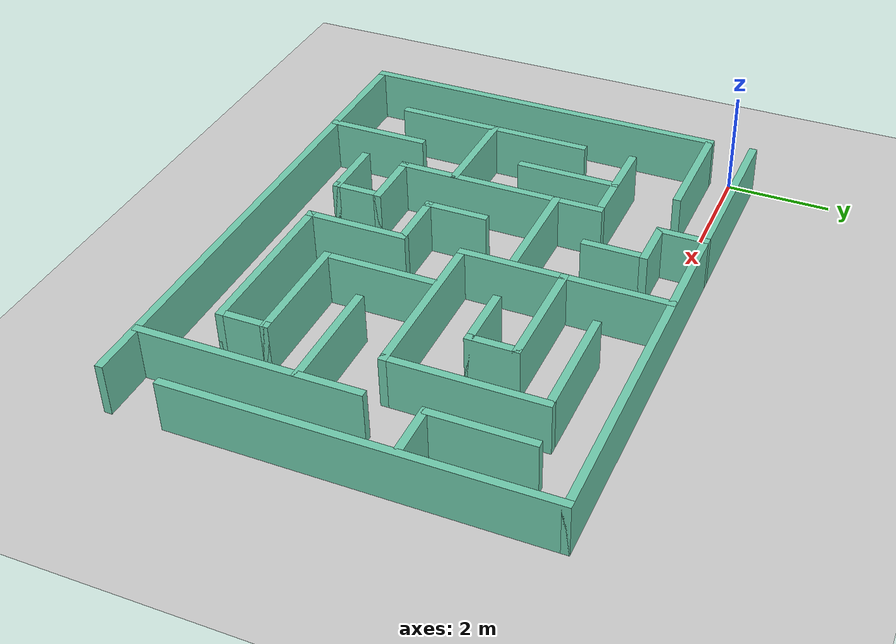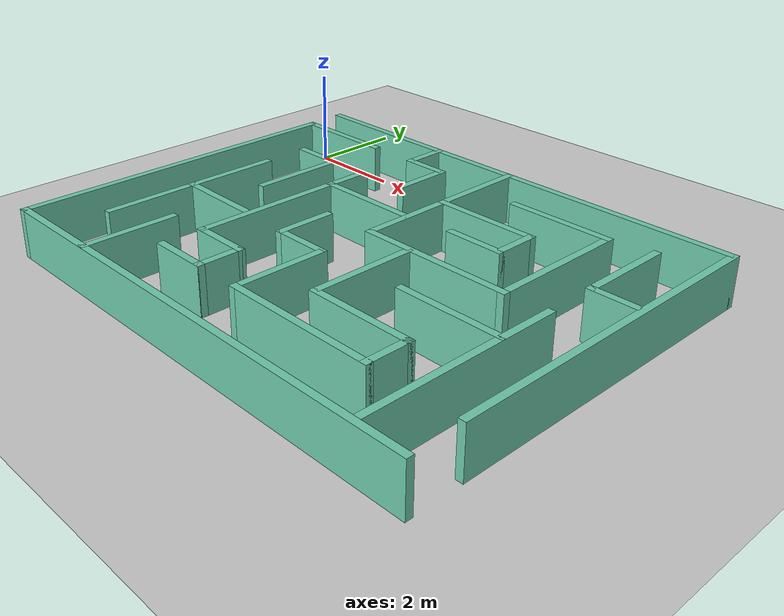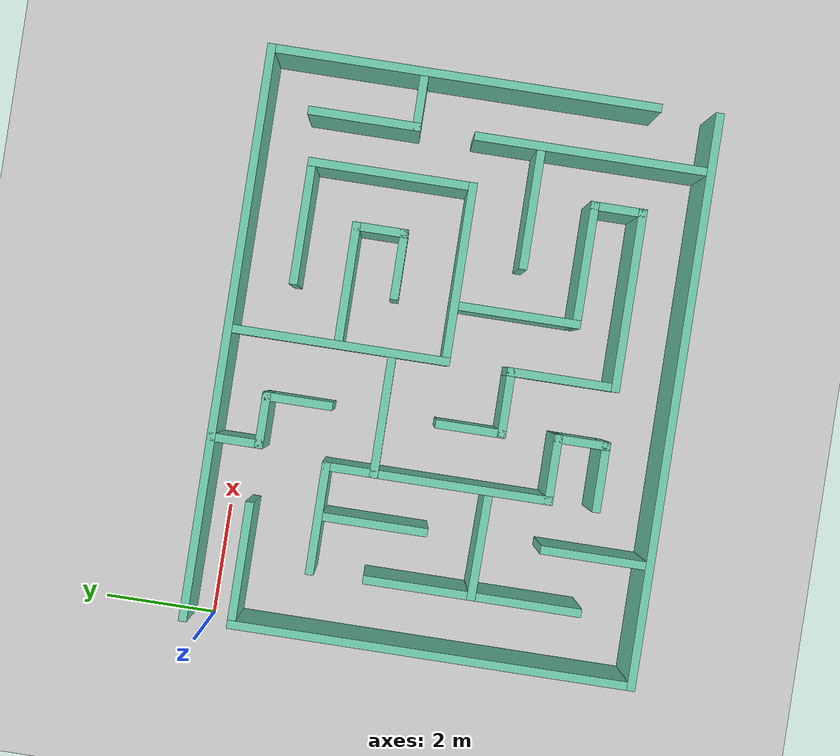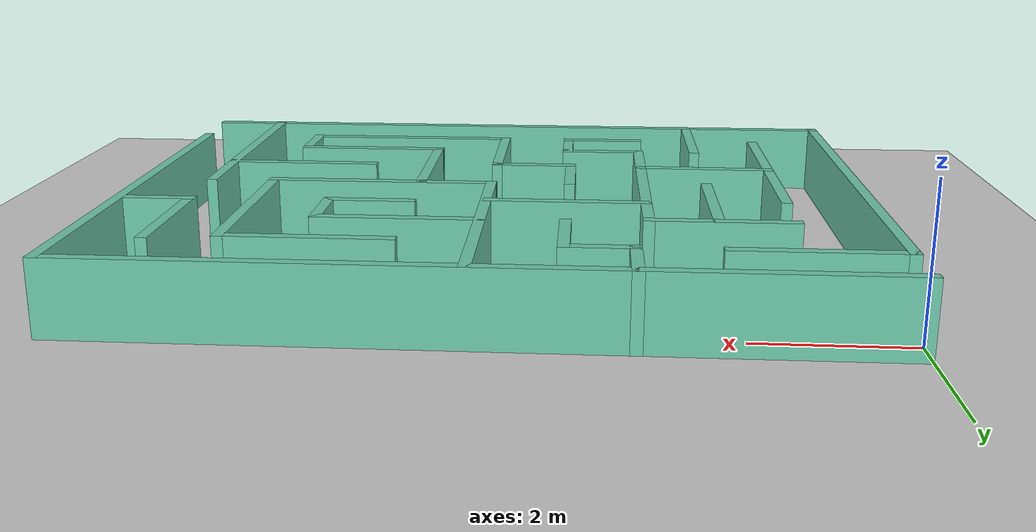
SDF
<sdf version="1.7">
 <world name="default">
  <light name="sun" type="directional">
   <pose>0 0 10 0 -0 0</pose>
   <diffuse>0.8 0.8 0.8 1</diffuse>
   <specular>0.2 0.2 0.2 1</specular>
   <attenuation>
    <range>1000</range>
    <constant>0.9</constant>
    <linear>0.01</linear>
    <quadratic>0.001</quadratic>
   </attenuation>
   <direction>-0.5 0.1 -0.9</direction>
   <spot><inner_angle>0</inner_angle><outer_angle>0</outer_angle><falloff>0</falloff></spot>
  </light>
  <model name="ground_plane">
   <static>1</static>
   <link name="link">
    <collision name="collision">
     <geometry><plane><normal>0 0 1</normal><size>100 100</size></plane></geometry>
     <surface><friction><ode><mu>100</mu><mu2>50</mu2></ode></friction></surface>
    </collision>
    <visual name="visual">
     <cast_shadows>0</cast_shadows>
     <geometry><plane><normal>0 0 1</normal><size>100 100</size></plane></geometry>
     <material>
      <script><uri>file://media/materials/scripts/gazebo.material</uri><name>Gazebo/Grey</name></script>
     </material>
    </visual>
   </link>
  </model>
  <gravity>0 0 -9.8</gravity>
  <magnetic_field>6e-06 2.3e-05 -4.2e-05</magnetic_field>
  <atmosphere type="adiabatic"/>
  <physics name="default_physics" default="0" type="ode">
   <max_step_size>0.001</max_step_size>
   <real_time_factor>1</real_time_factor>
   <real_time_update_rate>1000</real_time_update_rate>
  </physics>
  <scene><ambient>0.7 0.7 0.7 1</ambient><background>0.7 0.7 0.7 1</background><shadows>1</shadows></scene>
  <audio><device>default</device></audio>
  <spherical_coordinates>
   <surface_model>EARTH_WGS84</surface_model>
   <latitude_deg>0</latitude_deg>
   <longitude_deg>0</longitude_deg>
   <elevation>0</elevation>
   <heading_deg>0</heading_deg>
  </spherical_coordinates>
  <model name="maze">
   <link name="Wall_195">
    <pose>3.975 0 0 0 0 -1.5708</pose>
    <visual name="Wall_195_Visual">
     <pose>0 0 0.5 0 -0 0</pose>
     <geometry><box><size>10.25 0.15 1</size></box></geometry>
     <material>
      <script><uri>file://media/materials/scripts/gazebo.material</uri><name>Gazebo/Grey</name></script>
      <ambient>0.435294 0.796078 0.67451 1</ambient>
      <shader type="pixel"/>
     </material>
     <meta><layer>0</layer></meta>
    </visual>
    <collision name="Wall_195_Collision">
     <pose>0 0 0.5 0 -0 0</pose>
     <geometry><box><size>10.25 0.15 1</size></box></geometry>
     <surface>
      <friction>
       <ode><mu>1</mu><mu2>1</mu2><fdir1>0 0 0</fdir1><slip1>0</slip1><slip2>0</slip2></ode>
       <torsional>
        <coefficient>1</coefficient>
        <patch_radius>0</patch_radius>
        <surface_radius>0</surface_radius>
        <use_patch_radius>1</use_patch_radius>
        <ode><slip>0</slip></ode>
       </torsional>
      </friction>
      <bounce><restitution_coefficient>0</restitution_coefficient><threshold>1e+06</threshold></bounce>
      <contact>
       <collide_without_contact>0</collide_without_contact>
       <collide_without_contact_bitmask>1</collide_without_contact_bitmask>
       <collide_bitmask>1</collide_bitmask>
       <ode>
        <soft_cfm>0</soft_cfm>
        <soft_erp>0.2</soft_erp>
        <kp>1e+13</kp>
        <kd>1</kd>
        <max_vel>0.01</max_vel>
        <min_depth>0</min_depth>
       </ode>
       <bullet>
        <split_impulse>1</split_impulse>
        <split_impulse_penetration_threshold>-0.01</split_impulse_penetration_threshold>
        <soft_cfm>0</soft_cfm>
        <soft_erp>0.2</soft_erp>
        <kp>1e+13</kp>
        <kd>1</kd>
       </bullet>
      </contact>
     </surface>
    </collision>
   </link>
   <link name="Wall_196">
    <pose>0.425 -5.05 0 0 -0 3.14159</pose>
    <visual name="Wall_196_Visual">
     <pose>0 0 0.5 0 -0 0</pose>
     <geometry><box><size>7.25 0.15 1</size></box></geometry>
     <material>
      <script><uri>file://media/materials/scripts/gazebo.material</uri><name>Gazebo/Grey</name></script>
      <ambient>0.435294 0.796078 0.67451 1</ambient>
      <shader type="pixel"/>
     </material>
     <meta><layer>0</layer></meta>
    </visual>
    <collision name="Wall_196_Collision">
     <pose>0 0 0.5 0 -0 0</pose>
     <geometry><box><size>7.25 0.15 1</size></box></geometry>
     <surface>
      <friction>
       <ode><mu>1</mu><mu2>1</mu2><fdir1>0 0 0</fdir1><slip1>0</slip1><slip2>0</slip2></ode>
       <torsional>
        <coefficient>1</coefficient>
        <patch_radius>0</patch_radius>
        <surface_radius>0</surface_radius>
        <use_patch_radius>1</use_patch_radius>
        <ode><slip>0</slip></ode>
       </torsional>
      </friction>
      <bounce><restitution_coefficient>0</restitution_coefficient><threshold>1e+06</threshold></bounce>
      <contact>
       <collide_without_contact>0</collide_without_contact>
       <collide_without_contact_bitmask>1</collide_without_contact_bitmask>
       <collide_bitmask>1</collide_bitmask>
       <ode>
        <soft_cfm>0</soft_cfm>
        <soft_erp>0.2</soft_erp>
        <kp>1e+13</kp>
        <kd>1</kd>
        <max_vel>0.01</max_vel>
        <min_depth>0</min_depth>
       </ode>
       <bullet>
        <split_impulse>1</split_impulse>
        <split_impulse_penetration_threshold>-0.01</split_impulse_penetration_threshold>
        <soft_cfm>0</soft_cfm>
        <soft_erp>0.2</soft_erp>
        <kp>1e+13</kp>
        <kd>1</kd>
       </bullet>
      </contact>
     </surface>
    </collision>
   </link>
   <link name="Wall_198">
    <pose>-3.975 0 0 0 -0 1.5708</pose>
    <visual name="Wall_198_Visual">
     <pose>0 0 0.5 0 -0 0</pose>
     <geometry><box><size>10.25 0.15 1</size></box></geometry>
     <material>
      <script><uri>file://media/materials/scripts/gazebo.material</uri><name>Gazebo/Grey</name></script>
      <ambient>0.435294 0.796078 0.67451 1</ambient>
      <shader type="pixel"/>
     </material>
     <meta><layer>0</layer></meta>
    </visual>
    <collision name="Wall_198_Collision">
     <pose>0 0 0.5 0 -0 0</pose>
     <geometry><box><size>10.25 0.15 1</size></box></geometry>
     <surface>
      <friction>
       <ode><mu>1</mu><mu2>1</mu2><fdir1>0 0 0</fdir1><slip1>0</slip1><slip2>0</slip2></ode>
       <torsional>
        <coefficient>1</coefficient>
        <patch_radius>0</patch_radius>
        <surface_radius>0</surface_radius>
        <use_patch_radius>1</use_patch_radius>
        <ode><slip>0</slip></ode>
       </torsional>
      </friction>
      <bounce><restitution_coefficient>0</restitution_coefficient><threshold>1e+06</threshold></bounce>
      <contact>
       <collide_without_contact>0</collide_without_contact>
       <collide_without_contact_bitmask>1</collide_without_contact_bitmask>
       <collide_bitmask>1</collide_bitmask>
       <ode>
        <soft_cfm>0</soft_cfm>
        <soft_erp>0.2</soft_erp>
        <kp>1e+13</kp>
        <kd>1</kd>
        <max_vel>0.01</max_vel>
        <min_depth>0</min_depth>
       </ode>
       <bullet>
        <split_impulse>1</split_impulse>
        <split_impulse_penetration_threshold>-0.01</split_impulse_penetration_threshold>
        <soft_cfm>0</soft_cfm>
        <soft_erp>0.2</soft_erp>
        <kp>1e+13</kp>
        <kd>1</kd>
       </bullet>
      </contact>
     </surface>
    </collision>
   </link>
   <link name="Wall_201">
    <pose>-0.55 5.05 0 0 -0 0</pose>
    <visual name="Wall_201_Visual">
     <pose>0 0 0.5 0 -0 0</pose>
     <geometry><box><size>7 0.15 1</size></box></geometry>
     <material>
      <script><uri>file://media/materials/scripts/gazebo.material</uri><name>Gazebo/Grey</name></script>
      <ambient>0.435294 0.796078 0.67451 1</ambient>
      <shader type="pixel"/>
     </material>
     <meta><layer>0</layer></meta>
    </visual>
    <collision name="Wall_201_Collision">
     <pose>0 0 0.5 0 -0 0</pose>
     <geometry><box><size>7 0.15 1</size></box></geometry>
     <surface>
      <friction>
       <ode><mu>1</mu><mu2>1</mu2><fdir1>0 0 0</fdir1><slip1>0</slip1><slip2>0</slip2></ode>
       <torsional>
        <coefficient>1</coefficient>
        <patch_radius>0</patch_radius>
        <surface_radius>0</surface_radius>
        <use_patch_radius>1</use_patch_radius>
        <ode><slip>0</slip></ode>
       </torsional>
      </friction>
      <bounce><restitution_coefficient>0</restitution_coefficient><threshold>1e+06</threshold></bounce>
      <contact>
       <collide_without_contact>0</collide_without_contact>
       <collide_without_contact_bitmask>1</collide_without_contact_bitmask>
       <collide_bitmask>1</collide_bitmask>
       <ode>
        <soft_cfm>0</soft_cfm>
        <soft_erp>0.2</soft_erp>
        <kp>1e+13</kp>
        <kd>1</kd>
        <max_vel>0.01</max_vel>
        <min_depth>0</min_depth>
       </ode>
       <bullet>
        <split_impulse>1</split_impulse>
        <split_impulse_penetration_threshold>-0.01</split_impulse_penetration_threshold>
        <soft_cfm>0</soft_cfm>
        <soft_erp>0.2</soft_erp>
        <kp>1e+13</kp>
        <kd>1</kd>
       </bullet>
      </contact>
     </surface>
    </collision>
   </link>
   <link name="Wall_204">
    <pose>1.902 4.071 0 0 -0 3.14159</pose>
    <visual name="Wall_204_Visual">
     <pose>0 0 0.5 0 -0 0</pose>
     <geometry><box><size>4.25 0.15 1</size></box></geometry>
     <material>
      <script><uri>file://media/materials/scripts/gazebo.material</uri><name>Gazebo/Grey</name></script>
      <ambient>0.435294 0.796078 0.67451 1</ambient>
      <shader type="pixel"/>
     </material>
     <meta><layer>0</layer></meta>
    </visual>
    <collision name="Wall_204_Collision">
     <pose>0 0 0.5 0 -0 0</pose>
     <geometry><box><size>4.25 0.15 1</size></box></geometry>
     <surface>
      <friction>
       <ode><mu>1</mu><mu2>1</mu2><fdir1>0 0 0</fdir1><slip1>0</slip1><slip2>0</slip2></ode>
       <torsional>
        <coefficient>1</coefficient>
        <patch_radius>0</patch_radius>
        <surface_radius>0</surface_radius>
        <use_patch_radius>1</use_patch_radius>
        <ode><slip>0</slip></ode>
       </torsional>
      </friction>
      <bounce><restitution_coefficient>0</restitution_coefficient><threshold>1e+06</threshold></bounce>
      <contact>
       <collide_without_contact>0</collide_without_contact>
       <collide_without_contact_bitmask>1</collide_without_contact_bitmask>
       <collide_bitmask>1</collide_bitmask>
       <ode>
        <soft_cfm>0</soft_cfm>
        <soft_erp>0.2</soft_erp>
        <kp>1e+13</kp>
        <kd>1</kd>
        <max_vel>0.01</max_vel>
        <min_depth>0</min_depth>
       </ode>
       <bullet>
        <split_impulse>1</split_impulse>
        <split_impulse_penetration_threshold>-0.01</split_impulse_penetration_threshold>
        <soft_cfm>0</soft_cfm>
        <soft_erp>0.2</soft_erp>
        <kp>1e+13</kp>
        <kd>1</kd>
       </bullet>
      </contact>
     </surface>
    </collision>
   </link>
   <link name="Wall_209">
    <pose>-2.173 4.071 0 0 -0 3.14159</pose>
    <visual name="Wall_209_Visual">
     <pose>0 0 0.5 0 -0 0</pose>
     <geometry><box><size>2 0.15 1</size></box></geometry>
     <material>
      <script><uri>file://media/materials/scripts/gazebo.material</uri><name>Gazebo/Grey</name></script>
      <ambient>0.435294 0.796078 0.67451 1</ambient>
      <shader type="pixel"/>
     </material>
     <meta><layer>0</layer></meta>
    </visual>
    <collision name="Wall_209_Collision">
     <pose>0 0 0.5 0 -0 0</pose>
     <geometry><box><size>2 0.15 1</size></box></geometry>
     <surface>
      <friction>
       <ode><mu>1</mu><mu2>1</mu2><fdir1>0 0 0</fdir1><slip1>0</slip1><slip2>0</slip2></ode>
       <torsional>
        <coefficient>1</coefficient>
        <patch_radius>0</patch_radius>
        <surface_radius>0</surface_radius>
        <use_patch_radius>1</use_patch_radius>
        <ode><slip>0</slip></ode>
       </torsional>
      </friction>
      <bounce><restitution_coefficient>0</restitution_coefficient><threshold>1e+06</threshold></bounce>
      <contact>
       <collide_without_contact>0</collide_without_contact>
       <collide_without_contact_bitmask>1</collide_without_contact_bitmask>
       <collide_bitmask>1</collide_bitmask>
       <ode>
        <soft_cfm>0</soft_cfm>
        <soft_erp>0.2</soft_erp>
        <kp>1e+13</kp>
        <kd>1</kd>
        <max_vel>0.01</max_vel>
        <min_depth>0</min_depth>
       </ode>
       <bullet>
        <split_impulse>1</split_impulse>
        <split_impulse_penetration_threshold>-0.01</split_impulse_penetration_threshold>
        <soft_cfm>0</soft_cfm>
        <soft_erp>0.2</soft_erp>
        <kp>1e+13</kp>
        <kd>1</kd>
       </bullet>
      </contact>
     </surface>
    </collision>
   </link>
   <link name="Wall_211">
    <pose>0.975 3.012 0 0 0 -1.5708</pose>
    <visual name="Wall_211_Visual">
     <pose>0 0 0.5 0 -0 0</pose>
     <geometry><box><size>2.25 0.15 1</size></box></geometry>
     <material>
      <script><uri>file://media/materials/scripts/gazebo.material</uri><name>Gazebo/Grey</name></script>
      <ambient>0.435294 0.796078 0.67451 1</ambient>
      <shader type="pixel"/>
     </material>
     <meta><layer>0</layer></meta>
    </visual>
    <collision name="Wall_211_Collision">
     <pose>0 0 0.5 0 -0 0</pose>
     <geometry><box><size>2.25 0.15 1</size></box></geometry>
     <surface>
      <friction>
       <ode><mu>1</mu><mu2>1</mu2><fdir1>0 0 0</fdir1><slip1>0</slip1><slip2>0</slip2></ode>
       <torsional>
        <coefficient>1</coefficient>
        <patch_radius>0</patch_radius>
        <surface_radius>0</surface_radius>
        <use_patch_radius>1</use_patch_radius>
        <ode><slip>0</slip></ode>
       </torsional>
      </friction>
      <bounce><restitution_coefficient>0</restitution_coefficient><threshold>1e+06</threshold></bounce>
      <contact>
       <collide_without_contact>0</collide_without_contact>
       <collide_without_contact_bitmask>1</collide_without_contact_bitmask>
       <collide_bitmask>1</collide_bitmask>
       <ode>
        <soft_cfm>0</soft_cfm>
        <soft_erp>0.2</soft_erp>
        <kp>1e+13</kp>
        <kd>1</kd>
        <max_vel>0.01</max_vel>
        <min_depth>0</min_depth>
       </ode>
       <bullet>
        <split_impulse>1</split_impulse>
        <split_impulse_penetration_threshold>-0.01</split_impulse_penetration_threshold>
        <soft_cfm>0</soft_cfm>
        <soft_erp>0.2</soft_erp>
        <kp>1e+13</kp>
        <kd>1</kd>
       </bullet>
      </contact>
     </surface>
    </collision>
   </link>
   <link name="Wall_214">
    <pose>-2.038 0.084 0 0 -0 0</pose>
    <visual name="Wall_214_Visual">
     <pose>0 0 0.5 0 -0 0</pose>
     <geometry><box><size>4 0.15 1</size></box></geometry>
     <material>
      <script><uri>file://media/materials/scripts/gazebo.material</uri><name>Gazebo/Grey</name></script>
      <ambient>0.435294 0.796078 0.67451 1</ambient>
      <shader type="pixel"/>
     </material>
     <meta><layer>0</layer></meta>
    </visual>
    <collision name="Wall_214_Collision">
     <pose>0 0 0.5 0 -0 0</pose>
     <geometry><box><size>4 0.15 1</size></box></geometry>
     <surface>
      <friction>
       <ode><mu>1</mu><mu2>1</mu2><fdir1>0 0 0</fdir1><slip1>0</slip1><slip2>0</slip2></ode>
       <torsional>
        <coefficient>1</coefficient>
        <patch_radius>0</patch_radius>
        <surface_radius>0</surface_radius>
        <use_patch_radius>1</use_patch_radius>
        <ode><slip>0</slip></ode>
       </torsional>
      </friction>
      <bounce><restitution_coefficient>0</restitution_coefficient><threshold>1e+06</threshold></bounce>
      <contact>
       <collide_without_contact>0</collide_without_contact>
       <collide_without_contact_bitmask>1</collide_without_contact_bitmask>
       <collide_bitmask>1</collide_bitmask>
       <ode>
        <soft_cfm>0</soft_cfm>
        <soft_erp>0.2</soft_erp>
        <kp>1e+13</kp>
        <kd>1</kd>
        <max_vel>0.01</max_vel>
        <min_depth>0</min_depth>
       </ode>
       <bullet>
        <split_impulse>1</split_impulse>
        <split_impulse_penetration_threshold>-0.01</split_impulse_penetration_threshold>
        <soft_cfm>0</soft_cfm>
        <soft_erp>0.2</soft_erp>
        <kp>1e+13</kp>
        <kd>1</kd>
       </bullet>
      </contact>
     </surface>
    </collision>
   </link>
   <link name="Wall_217">
    <pose>-0.113 1.634 0 0 -0 1.5708</pose>
    <visual name="Wall_217_Visual">
     <pose>0 0 0.5 0 -0 0</pose>
     <geometry><box><size>3.25 0.15 1</size></box></geometry>
     <material>
      <script><uri>file://media/materials/scripts/gazebo.material</uri><name>Gazebo/Grey</name></script>
      <ambient>0.435294 0.796078 0.67451 1</ambient>
      <shader type="pixel"/>
     </material>
     <meta><layer>0</layer></meta>
    </visual>
    <collision name="Wall_217_Collision">
     <pose>0 0 0.5 0 -0 0</pose>
     <geometry><box><size>3.25 0.15 1</size></box></geometry>
     <surface>
      <friction>
       <ode><mu>1</mu><mu2>1</mu2><fdir1>0 0 0</fdir1><slip1>0</slip1><slip2>0</slip2></ode>
       <torsional>
        <coefficient>1</coefficient>
        <patch_radius>0</patch_radius>
        <surface_radius>0</surface_radius>
        <use_patch_radius>1</use_patch_radius>
        <ode><slip>0</slip></ode>
       </torsional>
      </friction>
      <bounce><restitution_coefficient>0</restitution_coefficient><threshold>1e+06</threshold></bounce>
      <contact>
       <collide_without_contact>0</collide_without_contact>
       <collide_without_contact_bitmask>1</collide_without_contact_bitmask>
       <collide_bitmask>1</collide_bitmask>
       <ode>
        <soft_cfm>0</soft_cfm>
        <soft_erp>0.2</soft_erp>
        <kp>1e+13</kp>
        <kd>1</kd>
        <max_vel>0.01</max_vel>
        <min_depth>0</min_depth>
       </ode>
       <bullet>
        <split_impulse>1</split_impulse>
        <split_impulse_penetration_threshold>-0.01</split_impulse_penetration_threshold>
        <soft_cfm>0</soft_cfm>
        <soft_erp>0.2</soft_erp>
        <kp>1e+13</kp>
        <kd>1</kd>
       </bullet>
      </contact>
     </surface>
    </collision>
   </link>
   <link name="Wall_218">
    <pose>-1.538 3.184 0 0 -0 3.14159</pose>
    <visual name="Wall_218_Visual">
     <pose>0 0 0.5 0 -0 0</pose>
     <geometry><box><size>3 0.15 1</size></box></geometry>
     <material>
      <script><uri>file://media/materials/scripts/gazebo.material</uri><name>Gazebo/Grey</name></script>
      <ambient>0.435294 0.796078 0.67451 1</ambient>
      <shader type="pixel"/>
     </material>
     <meta><layer>0</layer></meta>
    </visual>
    <collision name="Wall_218_Collision">
     <pose>0 0 0.5 0 -0 0</pose>
     <geometry><box><size>3 0.15 1</size></box></geometry>
     <surface>
      <friction>
       <ode><mu>1</mu><mu2>1</mu2><fdir1>0 0 0</fdir1><slip1>0</slip1><slip2>0</slip2></ode>
       <torsional>
        <coefficient>1</coefficient>
        <patch_radius>0</patch_radius>
        <surface_radius>0</surface_radius>
        <use_patch_radius>1</use_patch_radius>
        <ode><slip>0</slip></ode>
       </torsional>
      </friction>
      <bounce><restitution_coefficient>0</restitution_coefficient><threshold>1e+06</threshold></bounce>
      <contact>
       <collide_without_contact>0</collide_without_contact>
       <collide_without_contact_bitmask>1</collide_without_contact_bitmask>
       <collide_bitmask>1</collide_bitmask>
       <ode>
        <soft_cfm>0</soft_cfm>
        <soft_erp>0.2</soft_erp>
        <kp>1e+13</kp>
        <kd>1</kd>
        <max_vel>0.01</max_vel>
        <min_depth>0</min_depth>
       </ode>
       <bullet>
        <split_impulse>1</split_impulse>
        <split_impulse_penetration_threshold>-0.01</split_impulse_penetration_threshold>
        <soft_cfm>0</soft_cfm>
        <soft_erp>0.2</soft_erp>
        <kp>1e+13</kp>
        <kd>1</kd>
       </bullet>
      </contact>
     </surface>
    </collision>
   </link>
   <link name="Wall_219">
    <pose>-2.963 2.134 0 0 0 -1.5708</pose>
    <visual name="Wall_219_Visual">
     <pose>0 0 0.5 0 -0 0</pose>
     <geometry><box><size>2.25 0.15 1</size></box></geometry>
     <material>
      <script><uri>file://media/materials/scripts/gazebo.material</uri><name>Gazebo/Grey</name></script>
      <ambient>0.435294 0.796078 0.67451 1</ambient>
      <shader type="pixel"/>
     </material>
     <meta><layer>0</layer></meta>
    </visual>
    <collision name="Wall_219_Collision">
     <pose>0 0 0.5 0 -0 0</pose>
     <geometry><box><size>2.25 0.15 1</size></box></geometry>
     <surface>
      <friction>
       <ode><mu>1</mu><mu2>1</mu2><fdir1>0 0 0</fdir1><slip1>0</slip1><slip2>0</slip2></ode>
       <torsional>
        <coefficient>1</coefficient>
        <patch_radius>0</patch_radius>
        <surface_radius>0</surface_radius>
        <use_patch_radius>1</use_patch_radius>
        <ode><slip>0</slip></ode>
       </torsional>
      </friction>
      <bounce><restitution_coefficient>0</restitution_coefficient><threshold>1e+06</threshold></bounce>
      <contact>
       <collide_without_contact>0</collide_without_contact>
       <collide_without_contact_bitmask>1</collide_without_contact_bitmask>
       <collide_bitmask>1</collide_bitmask>
       <ode>
        <soft_cfm>0</soft_cfm>
        <soft_erp>0.2</soft_erp>
        <kp>1e+13</kp>
        <kd>1</kd>
        <max_vel>0.01</max_vel>
        <min_depth>0</min_depth>
       </ode>
       <bullet>
        <split_impulse>1</split_impulse>
        <split_impulse_penetration_threshold>-0.01</split_impulse_penetration_threshold>
        <soft_cfm>0</soft_cfm>
        <soft_erp>0.2</soft_erp>
        <kp>1e+13</kp>
        <kd>1</kd>
       </bullet>
      </contact>
     </surface>
    </collision>
   </link>
   <link name="Wall_221">
    <pose>-2.026 1.14 0 0 -0 1.5708</pose>
    <visual name="Wall_221_Visual">
     <pose>0 0 0.5 0 -0 0</pose>
     <geometry><box><size>2.25 0.15 1</size></box></geometry>
     <material>
      <script><uri>file://media/materials/scripts/gazebo.material</uri><name>Gazebo/Grey</name></script>
      <ambient>0.435294 0.796078 0.67451 1</ambient>
      <shader type="pixel"/>
     </material>
     <meta><layer>0</layer></meta>
    </visual>
    <collision name="Wall_221_Collision">
     <pose>0 0 0.5 0 -0 0</pose>
     <geometry><box><size>2.25 0.15 1</size></box></geometry>
     <surface>
      <friction>
       <ode><mu>1</mu><mu2>1</mu2><fdir1>0 0 0</fdir1><slip1>0</slip1><slip2>0</slip2></ode>
       <torsional>
        <coefficient>1</coefficient>
        <patch_radius>0</patch_radius>
        <surface_radius>0</surface_radius>
        <use_patch_radius>1</use_patch_radius>
        <ode><slip>0</slip></ode>
       </torsional>
      </friction>
      <bounce><restitution_coefficient>0</restitution_coefficient><threshold>1e+06</threshold></bounce>
      <contact>
       <collide_without_contact>0</collide_without_contact>
       <collide_without_contact_bitmask>1</collide_without_contact_bitmask>
       <collide_bitmask>1</collide_bitmask>
       <ode>
        <soft_cfm>0</soft_cfm>
        <soft_erp>0.2</soft_erp>
        <kp>1e+13</kp>
        <kd>1</kd>
        <max_vel>0.01</max_vel>
        <min_depth>0</min_depth>
       </ode>
       <bullet>
        <split_impulse>1</split_impulse>
        <split_impulse_penetration_threshold>-0.01</split_impulse_penetration_threshold>
        <soft_cfm>0</soft_cfm>
        <soft_erp>0.2</soft_erp>
        <kp>1e+13</kp>
        <kd>1</kd>
       </bullet>
      </contact>
     </surface>
    </collision>
   </link>
   <link name="Wall_223">
    <pose>-1.601 2.19 0 0 -0 0</pose>
    <visual name="Wall_223_Visual">
     <pose>0 0 0.5 0 -0 0</pose>
     <geometry><box><size>1 0.15 1</size></box></geometry>
     <material>
      <script><uri>file://media/materials/scripts/gazebo.material</uri><name>Gazebo/Grey</name></script>
      <ambient>0.435294 0.796078 0.67451 1</ambient>
      <shader type="pixel"/>
     </material>
     <meta><layer>0</layer></meta>
    </visual>
    <collision name="Wall_223_Collision">
     <pose>0 0 0.5 0 -0 0</pose>
     <geometry><box><size>1 0.15 1</size></box></geometry>
     <surface>
      <friction>
       <ode><mu>1</mu><mu2>1</mu2><fdir1>0 0 0</fdir1><slip1>0</slip1><slip2>0</slip2></ode>
       <torsional>
        <coefficient>1</coefficient>
        <patch_radius>0</patch_radius>
        <surface_radius>0</surface_radius>
        <use_patch_radius>1</use_patch_radius>
        <ode><slip>0</slip></ode>
       </torsional>
      </friction>
      <bounce><restitution_coefficient>0</restitution_coefficient><threshold>1e+06</threshold></bounce>
      <contact>
       <collide_without_contact>0</collide_without_contact>
       <collide_without_contact_bitmask>1</collide_without_contact_bitmask>
       <collide_bitmask>1</collide_bitmask>
       <ode>
        <soft_cfm>0</soft_cfm>
        <soft_erp>0.2</soft_erp>
        <kp>1e+13</kp>
        <kd>1</kd>
        <max_vel>0.01</max_vel>
        <min_depth>0</min_depth>
       </ode>
       <bullet>
        <split_impulse>1</split_impulse>
        <split_impulse_penetration_threshold>-0.01</split_impulse_penetration_threshold>
        <soft_cfm>0</soft_cfm>
        <soft_erp>0.2</soft_erp>
        <kp>1e+13</kp>
        <kd>1</kd>
       </bullet>
      </contact>
     </surface>
    </collision>
   </link>
   <link name="Wall_224">
    <pose>-1.176 1.64 0 0 0 -1.5708</pose>
    <visual name="Wall_224_Visual">
     <pose>0 0 0.5 0 -0 0</pose>
     <geometry><box><size>1.25 0.15 1</size></box></geometry>
     <material>
      <script><uri>file://media/materials/scripts/gazebo.material</uri><name>Gazebo/Grey</name></script>
      <ambient>0.435294 0.796078 0.67451 1</ambient>
      <shader type="pixel"/>
     </material>
     <meta><layer>0</layer></meta>
    </visual>
    <collision name="Wall_224_Collision">
     <pose>0 0 0.5 0 -0 0</pose>
     <geometry><box><size>1.25 0.15 1</size></box></geometry>
     <surface>
      <friction>
       <ode><mu>1</mu><mu2>1</mu2><fdir1>0 0 0</fdir1><slip1>0</slip1><slip2>0</slip2></ode>
       <torsional>
        <coefficient>1</coefficient>
        <patch_radius>0</patch_radius>
        <surface_radius>0</surface_radius>
        <use_patch_radius>1</use_patch_radius>
        <ode><slip>0</slip></ode>
       </torsional>
      </friction>
      <bounce><restitution_coefficient>0</restitution_coefficient><threshold>1e+06</threshold></bounce>
      <contact>
       <collide_without_contact>0</collide_without_contact>
       <collide_without_contact_bitmask>1</collide_without_contact_bitmask>
       <collide_bitmask>1</collide_bitmask>
       <ode>
        <soft_cfm>0</soft_cfm>
        <soft_erp>0.2</soft_erp>
        <kp>1e+13</kp>
        <kd>1</kd>
        <max_vel>0.01</max_vel>
        <min_depth>0</min_depth>
       </ode>
       <bullet>
        <split_impulse>1</split_impulse>
        <split_impulse_penetration_threshold>-0.01</split_impulse_penetration_threshold>
        <soft_cfm>0</soft_cfm>
        <soft_erp>0.2</soft_erp>
        <kp>1e+13</kp>
        <kd>1</kd>
       </bullet>
      </contact>
     </surface>
    </collision>
   </link>
   <link name="Wall_226">
    <pose>1.002 1.081 0 0 -0 0</pose>
    <visual name="Wall_226_Visual">
     <pose>0 0 0.5 0 -0 0</pose>
     <geometry><box><size>2.25 0.15 1</size></box></geometry>
     <material>
      <script><uri>file://media/materials/scripts/gazebo.material</uri><name>Gazebo/Grey</name></script>
      <ambient>0.435294 0.796078 0.67451 1</ambient>
      <shader type="pixel"/>
     </material>
     <meta><layer>0</layer></meta>
    </visual>
    <collision name="Wall_226_Collision">
     <pose>0 0 0.5 0 -0 0</pose>
     <geometry><box><size>2.25 0.15 1</size></box></geometry>
     <surface>
      <friction>
       <ode><mu>1</mu><mu2>1</mu2><fdir1>0 0 0</fdir1><slip1>0</slip1><slip2>0</slip2></ode>
       <torsional>
        <coefficient>1</coefficient>
        <patch_radius>0</patch_radius>
        <surface_radius>0</surface_radius>
        <use_patch_radius>1</use_patch_radius>
        <ode><slip>0</slip></ode>
       </torsional>
      </friction>
      <bounce><restitution_coefficient>0</restitution_coefficient><threshold>1e+06</threshold></bounce>
      <contact>
       <collide_without_contact>0</collide_without_contact>
       <collide_without_contact_bitmask>1</collide_without_contact_bitmask>
       <collide_bitmask>1</collide_bitmask>
       <ode>
        <soft_cfm>0</soft_cfm>
        <soft_erp>0.2</soft_erp>
        <kp>1e+13</kp>
        <kd>1</kd>
        <max_vel>0.01</max_vel>
        <min_depth>0</min_depth>
       </ode>
       <bullet>
        <split_impulse>1</split_impulse>
        <split_impulse_penetration_threshold>-0.01</split_impulse_penetration_threshold>
        <soft_cfm>0</soft_cfm>
        <soft_erp>0.2</soft_erp>
        <kp>1e+13</kp>
        <kd>1</kd>
       </bullet>
      </contact>
     </surface>
    </collision>
   </link>
   <link name="Wall_227">
    <pose>2.052 2.131 0 0 -0 1.5708</pose>
    <visual name="Wall_227_Visual">
     <pose>0 0 0.5 0 -0 0</pose>
     <geometry><box><size>2.25 0.15 1</size></box></geometry>
     <material>
      <script><uri>file://media/materials/scripts/gazebo.material</uri><name>Gazebo/Grey</name></script>
      <ambient>0.435294 0.796078 0.67451 1</ambient>
      <shader type="pixel"/>
     </material>
     <meta><layer>0</layer></meta>
    </visual>
    <collision name="Wall_227_Collision">
     <pose>0 0 0.5 0 -0 0</pose>
     <geometry><box><size>2.25 0.15 1</size></box></geometry>
     <surface>
      <friction>
       <ode><mu>1</mu><mu2>1</mu2><fdir1>0 0 0</fdir1><slip1>0</slip1><slip2>0</slip2></ode>
       <torsional>
        <coefficient>1</coefficient>
        <patch_radius>0</patch_radius>
        <surface_radius>0</surface_radius>
        <use_patch_radius>1</use_patch_radius>
        <ode><slip>0</slip></ode>
       </torsional>
      </friction>
      <bounce><restitution_coefficient>0</restitution_coefficient><threshold>1e+06</threshold></bounce>
      <contact>
       <collide_without_contact>0</collide_without_contact>
       <collide_without_contact_bitmask>1</collide_without_contact_bitmask>
       <collide_bitmask>1</collide_bitmask>
       <ode>
        <soft_cfm>0</soft_cfm>
        <soft_erp>0.2</soft_erp>
        <kp>1e+13</kp>
        <kd>1</kd>
        <max_vel>0.01</max_vel>
        <min_depth>0</min_depth>
       </ode>
       <bullet>
        <split_impulse>1</split_impulse>
        <split_impulse_penetration_threshold>-0.01</split_impulse_penetration_threshold>
        <soft_cfm>0</soft_cfm>
        <soft_erp>0.2</soft_erp>
        <kp>1e+13</kp>
        <kd>1</kd>
       </bullet>
      </contact>
     </surface>
    </collision>
   </link>
   <link name="Wall_228">
    <pose>2.477 3.181 0 0 -0 0</pose>
    <visual name="Wall_228_Visual">
     <pose>0 0 0.5 0 -0 0</pose>
     <geometry><box><size>1 0.15 1</size></box></geometry>
     <material>
      <script><uri>file://media/materials/scripts/gazebo.material</uri><name>Gazebo/Grey</name></script>
      <ambient>0.435294 0.796078 0.67451 1</ambient>
      <shader type="pixel"/>
     </material>
     <meta><layer>0</layer></meta>
    </visual>
    <collision name="Wall_228_Collision">
     <pose>0 0 0.5 0 -0 0</pose>
     <geometry><box><size>1 0.15 1</size></box></geometry>
     <surface>
      <friction>
       <ode><mu>1</mu><mu2>1</mu2><fdir1>0 0 0</fdir1><slip1>0</slip1><slip2>0</slip2></ode>
       <torsional>
        <coefficient>1</coefficient>
        <patch_radius>0</patch_radius>
        <surface_radius>0</surface_radius>
        <use_patch_radius>1</use_patch_radius>
        <ode><slip>0</slip></ode>
       </torsional>
      </friction>
      <bounce><restitution_coefficient>0</restitution_coefficient><threshold>1e+06</threshold></bounce>
      <contact>
       <collide_without_contact>0</collide_without_contact>
       <collide_without_contact_bitmask>1</collide_without_contact_bitmask>
       <collide_bitmask>1</collide_bitmask>
       <ode>
        <soft_cfm>0</soft_cfm>
        <soft_erp>0.2</soft_erp>
        <kp>1e+13</kp>
        <kd>1</kd>
        <max_vel>0.01</max_vel>
        <min_depth>0</min_depth>
       </ode>
       <bullet>
        <split_impulse>1</split_impulse>
        <split_impulse_penetration_threshold>-0.01</split_impulse_penetration_threshold>
        <soft_cfm>0</soft_cfm>
        <soft_erp>0.2</soft_erp>
        <kp>1e+13</kp>
        <kd>1</kd>
       </bullet>
      </contact>
     </surface>
    </collision>
   </link>
   <link name="Wall_229">
    <pose>2.902 1.631 0 0 0 -1.5708</pose>
    <visual name="Wall_229_Visual">
     <pose>0 0 0.5 0 -0 0</pose>
     <geometry><box><size>3.25 0.15 1</size></box></geometry>
     <material>
      <script><uri>file://media/materials/scripts/gazebo.material</uri><name>Gazebo/Grey</name></script>
      <ambient>0.435294 0.796078 0.67451 1</ambient>
      <shader type="pixel"/>
     </material>
     <meta><layer>0</layer></meta>
    </visual>
    <collision name="Wall_229_Collision">
     <pose>0 0 0.5 0 -0 0</pose>
     <geometry><box><size>3.25 0.15 1</size></box></geometry>
     <surface>
      <friction>
       <ode><mu>1</mu><mu2>1</mu2><fdir1>0 0 0</fdir1><slip1>0</slip1><slip2>0</slip2></ode>
       <torsional>
        <coefficient>1</coefficient>
        <patch_radius>0</patch_radius>
        <surface_radius>0</surface_radius>
        <use_patch_radius>1</use_patch_radius>
        <ode><slip>0</slip></ode>
       </torsional>
      </friction>
      <bounce><restitution_coefficient>0</restitution_coefficient><threshold>1e+06</threshold></bounce>
      <contact>
       <collide_without_contact>0</collide_without_contact>
       <collide_without_contact_bitmask>1</collide_without_contact_bitmask>
       <collide_bitmask>1</collide_bitmask>
       <ode>
        <soft_cfm>0</soft_cfm>
        <soft_erp>0.2</soft_erp>
        <kp>1e+13</kp>
        <kd>1</kd>
        <max_vel>0.01</max_vel>
        <min_depth>0</min_depth>
       </ode>
       <bullet>
        <split_impulse>1</split_impulse>
        <split_impulse_penetration_threshold>-0.01</split_impulse_penetration_threshold>
        <soft_cfm>0</soft_cfm>
        <soft_erp>0.2</soft_erp>
        <kp>1e+13</kp>
        <kd>1</kd>
       </bullet>
      </contact>
     </surface>
    </collision>
   </link>
   <link name="Wall_230">
    <pose>1.977 0.081 0 0 -0 3.14159</pose>
    <visual name="Wall_230_Visual">
     <pose>0 0 0.5 0 -0 0</pose>
     <geometry><box><size>2 0.15 1</size></box></geometry>
     <material>
      <script><uri>file://media/materials/scripts/gazebo.material</uri><name>Gazebo/Grey</name></script>
      <ambient>0.435294 0.796078 0.67451 1</ambient>
      <shader type="pixel"/>
     </material>
     <meta><layer>0</layer></meta>
    </visual>
    <collision name="Wall_230_Collision">
     <pose>0 0 0.5 0 -0 0</pose>
     <geometry><box><size>2 0.15 1</size></box></geometry>
     <surface>
      <friction>
       <ode><mu>1</mu><mu2>1</mu2><fdir1>0 0 0</fdir1><slip1>0</slip1><slip2>0</slip2></ode>
       <torsional>
        <coefficient>1</coefficient>
        <patch_radius>0</patch_radius>
        <surface_radius>0</surface_radius>
        <use_patch_radius>1</use_patch_radius>
        <ode><slip>0</slip></ode>
       </torsional>
      </friction>
      <bounce><restitution_coefficient>0</restitution_coefficient><threshold>1e+06</threshold></bounce>
      <contact>
       <collide_without_contact>0</collide_without_contact>
       <collide_without_contact_bitmask>1</collide_without_contact_bitmask>
       <collide_bitmask>1</collide_bitmask>
       <ode>
        <soft_cfm>0</soft_cfm>
        <soft_erp>0.2</soft_erp>
        <kp>1e+13</kp>
        <kd>1</kd>
        <max_vel>0.01</max_vel>
        <min_depth>0</min_depth>
       </ode>
       <bullet>
        <split_impulse>1</split_impulse>
        <split_impulse_penetration_threshold>-0.01</split_impulse_penetration_threshold>
        <soft_cfm>0</soft_cfm>
        <soft_erp>0.2</soft_erp>
        <kp>1e+13</kp>
        <kd>1</kd>
       </bullet>
      </contact>
     </surface>
    </collision>
   </link>
   <link name="Wall_231">
    <pose>1.052 -0.469 0 0 0 -1.5708</pose>
    <visual name="Wall_231_Visual">
     <pose>0 0 0.5 0 -0 0</pose>
     <geometry><box><size>1.25 0.15 1</size></box></geometry>
     <material>
      <script><uri>file://media/materials/scripts/gazebo.material</uri><name>Gazebo/Grey</name></script>
      <ambient>0.435294 0.796078 0.67451 1</ambient>
      <shader type="pixel"/>
     </material>
     <meta><layer>0</layer></meta>
    </visual>
    <collision name="Wall_231_Collision">
     <pose>0 0 0.5 0 -0 0</pose>
     <geometry><box><size>1.25 0.15 1</size></box></geometry>
     <surface>
      <friction>
       <ode><mu>1</mu><mu2>1</mu2><fdir1>0 0 0</fdir1><slip1>0</slip1><slip2>0</slip2></ode>
       <torsional>
        <coefficient>1</coefficient>
        <patch_radius>0</patch_radius>
        <surface_radius>0</surface_radius>
        <use_patch_radius>1</use_patch_radius>
        <ode><slip>0</slip></ode>
       </torsional>
      </friction>
      <bounce><restitution_coefficient>0</restitution_coefficient><threshold>1e+06</threshold></bounce>
      <contact>
       <collide_without_contact>0</collide_without_contact>
       <collide_without_contact_bitmask>1</collide_without_contact_bitmask>
       <collide_bitmask>1</collide_bitmask>
       <ode>
        <soft_cfm>0</soft_cfm>
        <soft_erp>0.2</soft_erp>
        <kp>1e+13</kp>
        <kd>1</kd>
        <max_vel>0.01</max_vel>
        <min_depth>0</min_depth>
       </ode>
       <bullet>
        <split_impulse>1</split_impulse>
        <split_impulse_penetration_threshold>-0.01</split_impulse_penetration_threshold>
        <soft_cfm>0</soft_cfm>
        <soft_erp>0.2</soft_erp>
        <kp>1e+13</kp>
        <kd>1</kd>
       </bullet>
      </contact>
     </surface>
    </collision>
   </link>
   <link name="Wall_232">
    <pose>0.502 -1.019 0 0 -0 3.14159</pose>
    <visual name="Wall_232_Visual">
     <pose>0 0 0.5 0 -0 0</pose>
     <geometry><box><size>1.25 0.15 1</size></box></geometry>
     <material>
      <script><uri>file://media/materials/scripts/gazebo.material</uri><name>Gazebo/Grey</name></script>
      <ambient>0.435294 0.796078 0.67451 1</ambient>
      <shader type="pixel"/>
     </material>
     <meta><layer>0</layer></meta>
    </visual>
    <collision name="Wall_232_Collision">
     <pose>0 0 0.5 0 -0 0</pose>
     <geometry><box><size>1.25 0.15 1</size></box></geometry>
     <surface>
      <friction>
       <ode><mu>1</mu><mu2>1</mu2><fdir1>0 0 0</fdir1><slip1>0</slip1><slip2>0</slip2></ode>
       <torsional>
        <coefficient>1</coefficient>
        <patch_radius>0</patch_radius>
        <surface_radius>0</surface_radius>
        <use_patch_radius>1</use_patch_radius>
        <ode><slip>0</slip></ode>
       </torsional>
      </friction>
      <bounce><restitution_coefficient>0</restitution_coefficient><threshold>1e+06</threshold></bounce>
      <contact>
       <collide_without_contact>0</collide_without_contact>
       <collide_without_contact_bitmask>1</collide_without_contact_bitmask>
       <collide_bitmask>1</collide_bitmask>
       <ode>
        <soft_cfm>0</soft_cfm>
        <soft_erp>0.2</soft_erp>
        <kp>1e+13</kp>
        <kd>1</kd>
        <max_vel>0.01</max_vel>
        <min_depth>0</min_depth>
       </ode>
       <bullet>
        <split_impulse>1</split_impulse>
        <split_impulse_penetration_threshold>-0.01</split_impulse_penetration_threshold>
        <soft_cfm>0</soft_cfm>
        <soft_erp>0.2</soft_erp>
        <kp>1e+13</kp>
        <kd>1</kd>
       </bullet>
      </contact>
     </surface>
    </collision>
   </link>
   <link name="Wall_234">
    <pose>-1.056 -1.002 0 0 0 -1.5708</pose>
    <visual name="Wall_234_Visual">
     <pose>0 0 0.5 0 -0 0</pose>
     <geometry><box><size>2.25 0.15 1</size></box></geometry>
     <material>
      <script><uri>file://media/materials/scripts/gazebo.material</uri><name>Gazebo/Grey</name></script>
      <ambient>0.435294 0.796078 0.67451 1</ambient>
      <shader type="pixel"/>
     </material>
     <meta><layer>0</layer></meta>
    </visual>
    <collision name="Wall_234_Collision">
     <pose>0 0 0.5 0 -0 0</pose>
     <geometry><box><size>2.25 0.15 1</size></box></geometry>
     <surface>
      <friction>
       <ode><mu>1</mu><mu2>1</mu2><fdir1>0 0 0</fdir1><slip1>0</slip1><slip2>0</slip2></ode>
       <torsional>
        <coefficient>1</coefficient>
        <patch_radius>0</patch_radius>
        <surface_radius>0</surface_radius>
        <use_patch_radius>1</use_patch_radius>
        <ode><slip>0</slip></ode>
       </torsional>
      </friction>
      <bounce><restitution_coefficient>0</restitution_coefficient><threshold>1e+06</threshold></bounce>
      <contact>
       <collide_without_contact>0</collide_without_contact>
       <collide_without_contact_bitmask>1</collide_without_contact_bitmask>
       <collide_bitmask>1</collide_bitmask>
       <ode>
        <soft_cfm>0</soft_cfm>
        <soft_erp>0.2</soft_erp>
        <kp>1e+13</kp>
        <kd>1</kd>
        <max_vel>0.01</max_vel>
        <min_depth>0</min_depth>
       </ode>
       <bullet>
        <split_impulse>1</split_impulse>
        <split_impulse_penetration_threshold>-0.01</split_impulse_penetration_threshold>
        <soft_cfm>0</soft_cfm>
        <soft_erp>0.2</soft_erp>
        <kp>1e+13</kp>
        <kd>1</kd>
       </bullet>
      </contact>
     </surface>
    </collision>
   </link>
   <link name="Wall_235">
    <pose>0.494 -2.052 0 0 -0 0</pose>
    <visual name="Wall_235_Visual">
     <pose>0 0 0.5 0 -0 0</pose>
     <geometry><box><size>3.25 0.15 1</size></box></geometry>
     <material>
      <script><uri>file://media/materials/scripts/gazebo.material</uri><name>Gazebo/Grey</name></script>
      <ambient>0.435294 0.796078 0.67451 1</ambient>
      <shader type="pixel"/>
     </material>
     <meta><layer>0</layer></meta>
    </visual>
    <collision name="Wall_235_Collision">
     <pose>0 0 0.5 0 -0 0</pose>
     <geometry><box><size>3.25 0.15 1</size></box></geometry>
     <surface>
      <friction>
       <ode><mu>1</mu><mu2>1</mu2><fdir1>0 0 0</fdir1><slip1>0</slip1><slip2>0</slip2></ode>
       <torsional>
        <coefficient>1</coefficient>
        <patch_radius>0</patch_radius>
        <surface_radius>0</surface_radius>
        <use_patch_radius>1</use_patch_radius>
        <ode><slip>0</slip></ode>
       </torsional>
      </friction>
      <bounce><restitution_coefficient>0</restitution_coefficient><threshold>1e+06</threshold></bounce>
      <contact>
       <collide_without_contact>0</collide_without_contact>
       <collide_without_contact_bitmask>1</collide_without_contact_bitmask>
       <collide_bitmask>1</collide_bitmask>
       <ode>
        <soft_cfm>0</soft_cfm>
        <soft_erp>0.2</soft_erp>
        <kp>1e+13</kp>
        <kd>1</kd>
        <max_vel>0.01</max_vel>
        <min_depth>0</min_depth>
       </ode>
       <bullet>
        <split_impulse>1</split_impulse>
        <split_impulse_penetration_threshold>-0.01</split_impulse_penetration_threshold>
        <soft_cfm>0</soft_cfm>
        <soft_erp>0.2</soft_erp>
        <kp>1e+13</kp>
        <kd>1</kd>
       </bullet>
      </contact>
     </surface>
    </collision>
   </link>
   <link name="Wall_236">
    <pose>2.044 -1.502 0 0 -0 1.5708</pose>
    <visual name="Wall_236_Visual">
     <pose>0 0 0.5 0 -0 0</pose>
     <geometry><box><size>1.25 0.15 1</size></box></geometry>
     <material>
      <script><uri>file://media/materials/scripts/gazebo.material</uri><name>Gazebo/Grey</name></script>
      <ambient>0.435294 0.796078 0.67451 1</ambient>
      <shader type="pixel"/>
     </material>
     <meta><layer>0</layer></meta>
    </visual>
    <collision name="Wall_236_Collision">
     <pose>0 0 0.5 0 -0 0</pose>
     <geometry><box><size>1.25 0.15 1</size></box></geometry>
     <surface>
      <friction>
       <ode><mu>1</mu><mu2>1</mu2><fdir1>0 0 0</fdir1><slip1>0</slip1><slip2>0</slip2></ode>
       <torsional>
        <coefficient>1</coefficient>
        <patch_radius>0</patch_radius>
        <surface_radius>0</surface_radius>
        <use_patch_radius>1</use_patch_radius>
        <ode><slip>0</slip></ode>
       </torsional>
      </friction>
      <bounce><restitution_coefficient>0</restitution_coefficient><threshold>1e+06</threshold></bounce>
      <contact>
       <collide_without_contact>0</collide_without_contact>
       <collide_without_contact_bitmask>1</collide_without_contact_bitmask>
       <collide_bitmask>1</collide_bitmask>
       <ode>
        <soft_cfm>0</soft_cfm>
        <soft_erp>0.2</soft_erp>
        <kp>1e+13</kp>
        <kd>1</kd>
        <max_vel>0.01</max_vel>
        <min_depth>0</min_depth>
       </ode>
       <bullet>
        <split_impulse>1</split_impulse>
        <split_impulse_penetration_threshold>-0.01</split_impulse_penetration_threshold>
        <soft_cfm>0</soft_cfm>
        <soft_erp>0.2</soft_erp>
        <kp>1e+13</kp>
        <kd>1</kd>
       </bullet>
      </contact>
     </surface>
    </collision>
   </link>
   <link name="Wall_237">
    <pose>2.469 -0.952 0 0 -0 0</pose>
    <visual name="Wall_237_Visual">
     <pose>0 0 0.5 0 -0 0</pose>
     <geometry><box><size>1 0.15 1</size></box></geometry>
     <material>
      <script><uri>file://media/materials/scripts/gazebo.material</uri><name>Gazebo/Grey</name></script>
      <ambient>0.435294 0.796078 0.67451 1</ambient>
      <shader type="pixel"/>
     </material>
     <meta><layer>0</layer></meta>
    </visual>
    <collision name="Wall_237_Collision">
     <pose>0 0 0.5 0 -0 0</pose>
     <geometry><box><size>1 0.15 1</size></box></geometry>
     <surface>
      <friction>
       <ode><mu>1</mu><mu2>1</mu2><fdir1>0 0 0</fdir1><slip1>0</slip1><slip2>0</slip2></ode>
       <torsional>
        <coefficient>1</coefficient>
        <patch_radius>0</patch_radius>
        <surface_radius>0</surface_radius>
        <use_patch_radius>1</use_patch_radius>
        <ode><slip>0</slip></ode>
       </torsional>
      </friction>
      <bounce><restitution_coefficient>0</restitution_coefficient><threshold>1e+06</threshold></bounce>
      <contact>
       <collide_without_contact>0</collide_without_contact>
       <collide_without_contact_bitmask>1</collide_without_contact_bitmask>
       <collide_bitmask>1</collide_bitmask>
       <ode>
        <soft_cfm>0</soft_cfm>
        <soft_erp>0.2</soft_erp>
        <kp>1e+13</kp>
        <kd>1</kd>
        <max_vel>0.01</max_vel>
        <min_depth>0</min_depth>
       </ode>
       <bullet>
        <split_impulse>1</split_impulse>
        <split_impulse_penetration_threshold>-0.01</split_impulse_penetration_threshold>
        <soft_cfm>0</soft_cfm>
        <soft_erp>0.2</soft_erp>
        <kp>1e+13</kp>
        <kd>1</kd>
       </bullet>
      </contact>
     </surface>
    </collision>
   </link>
   <link name="Wall_238">
    <pose>2.894 -1.502 0 0 0 -1.5708</pose>
    <visual name="Wall_238_Visual">
     <pose>0 0 0.5 0 -0 0</pose>
     <geometry><box><size>1.25 0.15 1</size></box></geometry>
     <material>
      <script><uri>file://media/materials/scripts/gazebo.material</uri><name>Gazebo/Grey</name></script>
      <ambient>0.435294 0.796078 0.67451 1</ambient>
      <shader type="pixel"/>
     </material>
     <meta><layer>0</layer></meta>
    </visual>
    <collision name="Wall_238_Collision">
     <pose>0 0 0.5 0 -0 0</pose>
     <geometry><box><size>1.25 0.15 1</size></box></geometry>
     <surface>
      <friction>
       <ode><mu>1</mu><mu2>1</mu2><fdir1>0 0 0</fdir1><slip1>0</slip1><slip2>0</slip2></ode>
       <torsional>
        <coefficient>1</coefficient>
        <patch_radius>0</patch_radius>
        <surface_radius>0</surface_radius>
        <use_patch_radius>1</use_patch_radius>
        <ode><slip>0</slip></ode>
       </torsional>
      </friction>
      <bounce><restitution_coefficient>0</restitution_coefficient><threshold>1e+06</threshold></bounce>
      <contact>
       <collide_without_contact>0</collide_without_contact>
       <collide_without_contact_bitmask>1</collide_without_contact_bitmask>
       <collide_bitmask>1</collide_bitmask>
       <ode>
        <soft_cfm>0</soft_cfm>
        <soft_erp>0.2</soft_erp>
        <kp>1e+13</kp>
        <kd>1</kd>
        <max_vel>0.01</max_vel>
        <min_depth>0</min_depth>
       </ode>
       <bullet>
        <split_impulse>1</split_impulse>
        <split_impulse_penetration_threshold>-0.01</split_impulse_penetration_threshold>
        <soft_cfm>0</soft_cfm>
        <soft_erp>0.2</soft_erp>
        <kp>1e+13</kp>
        <kd>1</kd>
       </bullet>
      </contact>
     </surface>
    </collision>
   </link>
   <link name="Wall_241">
    <pose>3.033 -2.919 0 0 -0 3.14159</pose>
    <visual name="Wall_241_Visual">
     <pose>0 0 0.5 0 -0 0</pose>
     <geometry><box><size>2 0.15 1</size></box></geometry>
     <material>
      <script><uri>file://media/materials/scripts/gazebo.material</uri><name>Gazebo/Grey</name></script>
      <ambient>0.435294 0.796078 0.67451 1</ambient>
      <shader type="pixel"/>
     </material>
     <meta><layer>0</layer></meta>
    </visual>
    <collision name="Wall_241_Collision">
     <pose>0 0 0.5 0 -0 0</pose>
     <geometry><box><size>2 0.15 1</size></box></geometry>
     <surface>
      <friction>
       <ode><mu>1</mu><mu2>1</mu2><fdir1>0 0 0</fdir1><slip1>0</slip1><slip2>0</slip2></ode>
       <torsional>
        <coefficient>1</coefficient>
        <patch_radius>0</patch_radius>
        <surface_radius>0</surface_radius>
        <use_patch_radius>1</use_patch_radius>
        <ode><slip>0</slip></ode>
       </torsional>
      </friction>
      <bounce><restitution_coefficient>0</restitution_coefficient><threshold>1e+06</threshold></bounce>
      <contact>
       <collide_without_contact>0</collide_without_contact>
       <collide_without_contact_bitmask>1</collide_without_contact_bitmask>
       <collide_bitmask>1</collide_bitmask>
       <ode>
        <soft_cfm>0</soft_cfm>
        <soft_erp>0.2</soft_erp>
        <kp>1e+13</kp>
        <kd>1</kd>
        <max_vel>0.01</max_vel>
        <min_depth>0</min_depth>
       </ode>
       <bullet>
        <split_impulse>1</split_impulse>
        <split_impulse_penetration_threshold>-0.01</split_impulse_penetration_threshold>
        <soft_cfm>0</soft_cfm>
        <soft_erp>0.2</soft_erp>
        <kp>1e+13</kp>
        <kd>1</kd>
       </bullet>
      </contact>
     </surface>
    </collision>
   </link>
   <link name="Wall_243">
    <pose>-1.481 -2.052 0 0 -0 3.14159</pose>
    <visual name="Wall_243_Visual">
     <pose>0 0 0.5 0 -0 0</pose>
     <geometry><box><size>1 0.15 1</size></box></geometry>
     <material>
      <script><uri>file://media/materials/scripts/gazebo.material</uri><name>Gazebo/Grey</name></script>
      <ambient>0.435294 0.796078 0.67451 1</ambient>
      <shader type="pixel"/>
     </material>
     <meta><layer>0</layer></meta>
    </visual>
    <collision name="Wall_243_Collision">
     <pose>0 0 0.5 0 -0 0</pose>
     <geometry><box><size>1 0.15 1</size></box></geometry>
     <surface>
      <friction>
       <ode><mu>1</mu><mu2>1</mu2><fdir1>0 0 0</fdir1><slip1>0</slip1><slip2>0</slip2></ode>
       <torsional>
        <coefficient>1</coefficient>
        <patch_radius>0</patch_radius>
        <surface_radius>0</surface_radius>
        <use_patch_radius>1</use_patch_radius>
        <ode><slip>0</slip></ode>
       </torsional>
      </friction>
      <bounce><restitution_coefficient>0</restitution_coefficient><threshold>1e+06</threshold></bounce>
      <contact>
       <collide_without_contact>0</collide_without_contact>
       <collide_without_contact_bitmask>1</collide_without_contact_bitmask>
       <collide_bitmask>1</collide_bitmask>
       <ode>
        <soft_cfm>0</soft_cfm>
        <soft_erp>0.2</soft_erp>
        <kp>1e+13</kp>
        <kd>1</kd>
        <max_vel>0.01</max_vel>
        <min_depth>0</min_depth>
       </ode>
       <bullet>
        <split_impulse>1</split_impulse>
        <split_impulse_penetration_threshold>-0.01</split_impulse_penetration_threshold>
        <soft_cfm>0</soft_cfm>
        <soft_erp>0.2</soft_erp>
        <kp>1e+13</kp>
        <kd>1</kd>
       </bullet>
      </contact>
     </surface>
    </collision>
   </link>
   <link name="Wall_244">
    <pose>-1.906 -2.977 0 0 0 -1.5708</pose>
    <visual name="Wall_244_Visual">
     <pose>0 0 0.5 0 -0 0</pose>
     <geometry><box><size>2 0.15 1</size></box></geometry>
     <material>
      <script><uri>file://media/materials/scripts/gazebo.material</uri><name>Gazebo/Grey</name></script>
      <ambient>0.435294 0.796078 0.67451 1</ambient>
      <shader type="pixel"/>
     </material>
     <meta><layer>0</layer></meta>
    </visual>
    <collision name="Wall_244_Collision">
     <pose>0 0 0.5 0 -0 0</pose>
     <geometry><box><size>2 0.15 1</size></box></geometry>
     <surface>
      <friction>
       <ode><mu>1</mu><mu2>1</mu2><fdir1>0 0 0</fdir1><slip1>0</slip1><slip2>0</slip2></ode>
       <torsional>
        <coefficient>1</coefficient>
        <patch_radius>0</patch_radius>
        <surface_radius>0</surface_radius>
        <use_patch_radius>1</use_patch_radius>
        <ode><slip>0</slip></ode>
       </torsional>
      </friction>
      <bounce><restitution_coefficient>0</restitution_coefficient><threshold>1e+06</threshold></bounce>
      <contact>
       <collide_without_contact>0</collide_without_contact>
       <collide_without_contact_bitmask>1</collide_without_contact_bitmask>
       <collide_bitmask>1</collide_bitmask>
       <ode>
        <soft_cfm>0</soft_cfm>
        <soft_erp>0.2</soft_erp>
        <kp>1e+13</kp>
        <kd>1</kd>
        <max_vel>0.01</max_vel>
        <min_depth>0</min_depth>
       </ode>
       <bullet>
        <split_impulse>1</split_impulse>
        <split_impulse_penetration_threshold>-0.01</split_impulse_penetration_threshold>
        <soft_cfm>0</soft_cfm>
        <soft_erp>0.2</soft_erp>
        <kp>1e+13</kp>
        <kd>1</kd>
       </bullet>
      </contact>
     </surface>
    </collision>
   </link>
   <link name="Wall_246">
    <pose>-0.966 -2.933 0 0 -0 3.14159</pose>
    <visual name="Wall_246_Visual">
     <pose>0 0 0.5 0 -0 0</pose>
     <geometry><box><size>2 0.15 1</size></box></geometry>
     <material>
      <script><uri>file://media/materials/scripts/gazebo.material</uri><name>Gazebo/Grey</name></script>
      <ambient>0.435294 0.796078 0.67451 1</ambient>
      <shader type="pixel"/>
     </material>
     <meta><layer>0</layer></meta>
    </visual>
    <collision name="Wall_246_Collision">
     <pose>0 0 0.5 0 -0 0</pose>
     <geometry><box><size>2 0.15 1</size></box></geometry>
     <surface>
      <friction>
       <ode><mu>1</mu><mu2>1</mu2><fdir1>0 0 0</fdir1><slip1>0</slip1><slip2>0</slip2></ode>
       <torsional>
        <coefficient>1</coefficient>
        <patch_radius>0</patch_radius>
        <surface_radius>0</surface_radius>
        <use_patch_radius>1</use_patch_radius>
        <ode><slip>0</slip></ode>
       </torsional>
      </friction>
      <bounce><restitution_coefficient>0</restitution_coefficient><threshold>1e+06</threshold></bounce>
      <contact>
       <collide_without_contact>0</collide_without_contact>
       <collide_without_contact_bitmask>1</collide_without_contact_bitmask>
       <collide_bitmask>1</collide_bitmask>
       <ode>
        <soft_cfm>0</soft_cfm>
        <soft_erp>0.2</soft_erp>
        <kp>1e+13</kp>
        <kd>1</kd>
        <max_vel>0.01</max_vel>
        <min_depth>0</min_depth>
       </ode>
       <bullet>
        <split_impulse>1</split_impulse>
        <split_impulse_penetration_threshold>-0.01</split_impulse_penetration_threshold>
        <soft_cfm>0</soft_cfm>
        <soft_erp>0.2</soft_erp>
        <kp>1e+13</kp>
        <kd>1</kd>
       </bullet>
      </contact>
     </surface>
    </collision>
   </link>
   <link name="Wall_253">
    <pose>0.9745 -2.989 0 0 0 -1.58539</pose>
    <visual name="Wall_253_Visual">
     <pose>0 0 0.5 0 -0 0</pose>
     <geometry><box><size>2 0.15 1</size></box></geometry>
     <material>
      <script><uri>file://media/materials/scripts/gazebo.material</uri><name>Gazebo/Grey</name></script>
      <ambient>0.435294 0.796078 0.67451 1</ambient>
      <shader type="pixel"/>
     </material>
     <meta><layer>0</layer></meta>
    </visual>
    <collision name="Wall_253_Collision">
     <pose>0 0 0.5 0 -0 0</pose>
     <geometry><box><size>2 0.15 1</size></box></geometry>
     <surface>
      <friction>
       <ode><mu>1</mu><mu2>1</mu2><fdir1>0 0 0</fdir1><slip1>0</slip1><slip2>0</slip2></ode>
       <torsional>
        <coefficient>1</coefficient>
        <patch_radius>0</patch_radius>
        <surface_radius>0</surface_radius>
        <use_patch_radius>1</use_patch_radius>
        <ode><slip>0</slip></ode>
       </torsional>
      </friction>
      <bounce><restitution_coefficient>0</restitution_coefficient><threshold>1e+06</threshold></bounce>
      <contact>
       <collide_without_contact>0</collide_without_contact>
       <collide_without_contact_bitmask>1</collide_without_contact_bitmask>
       <collide_bitmask>1</collide_bitmask>
       <ode>
        <soft_cfm>0</soft_cfm>
        <soft_erp>0.2</soft_erp>
        <kp>1e+13</kp>
        <kd>1</kd>
        <max_vel>0.01</max_vel>
        <min_depth>0</min_depth>
       </ode>
       <bullet>
        <split_impulse>1</split_impulse>
        <split_impulse_penetration_threshold>-0.01</split_impulse_penetration_threshold>
        <soft_cfm>0</soft_cfm>
        <soft_erp>0.2</soft_erp>
        <kp>1e+13</kp>
        <kd>1</kd>
       </bullet>
      </contact>
     </surface>
    </collision>
   </link>
   <link name="Wall_254">
    <pose>0.036 -3.914 0 0 -0 3.14159</pose>
    <visual name="Wall_254_Visual">
     <pose>0 0 0.5 0 -0 0</pose>
     <geometry><box><size>2 0.15 1</size></box></geometry>
     <material>
      <script><uri>file://media/materials/scripts/gazebo.material</uri><name>Gazebo/Grey</name></script>
      <ambient>0.435294 0.796078 0.67451 1</ambient>
      <shader type="pixel"/>
     </material>
     <meta><layer>0</layer></meta>
    </visual>
    <collision name="Wall_254_Collision">
     <pose>0 0 0.5 0 -0 0</pose>
     <geometry><box><size>2 0.15 1</size></box></geometry>
     <surface>
      <friction>
       <ode><mu>1</mu><mu2>1</mu2><fdir1>0 0 0</fdir1><slip1>0</slip1><slip2>0</slip2></ode>
       <torsional>
        <coefficient>1</coefficient>
        <patch_radius>0</patch_radius>
        <surface_radius>0</surface_radius>
        <use_patch_radius>1</use_patch_radius>
        <ode><slip>0</slip></ode>
       </torsional>
      </friction>
      <bounce><restitution_coefficient>0</restitution_coefficient><threshold>1e+06</threshold></bounce>
      <contact>
       <collide_without_contact>0</collide_without_contact>
       <collide_without_contact_bitmask>1</collide_without_contact_bitmask>
       <collide_bitmask>1</collide_bitmask>
       <ode>
        <soft_cfm>0</soft_cfm>
        <soft_erp>0.2</soft_erp>
        <kp>1e+13</kp>
        <kd>1</kd>
        <max_vel>0.01</max_vel>
        <min_depth>0</min_depth>
       </ode>
       <bullet>
        <split_impulse>1</split_impulse>
        <split_impulse_penetration_threshold>-0.01</split_impulse_penetration_threshold>
        <soft_cfm>0</soft_cfm>
        <soft_erp>0.2</soft_erp>
        <kp>1e+13</kp>
        <kd>1</kd>
       </bullet>
      </contact>
     </surface>
    </collision>
   </link>
   <link name="Wall_256">
    <pose>1.8995 -3.914 0 0 -0 0</pose>
    <visual name="Wall_256_Visual">
     <pose>0 0 0.5 0 -0 0</pose>
     <geometry><box><size>2.02677 0.15 1</size></box></geometry>
     <material>
      <script><uri>file://media/materials/scripts/gazebo.material</uri><name>Gazebo/Grey</name></script>
      <ambient>0.435294 0.796078 0.67451 1</ambient>
      <shader type="pixel"/>
     </material>
     <meta><layer>0</layer></meta>
    </visual>
    <collision name="Wall_256_Collision">
     <pose>0 0 0.5 0 -0 0</pose>
     <geometry><box><size>2.02677 0.15 1</size></box></geometry>
     <surface>
      <friction>
       <ode><mu>1</mu><mu2>1</mu2><fdir1>0 0 0</fdir1><slip1>0</slip1><slip2>0</slip2></ode>
       <torsional>
        <coefficient>1</coefficient>
        <patch_radius>0</patch_radius>
        <surface_radius>0</surface_radius>
        <use_patch_radius>1</use_patch_radius>
        <ode><slip>0</slip></ode>
       </torsional>
      </friction>
      <bounce><restitution_coefficient>0</restitution_coefficient><threshold>1e+06</threshold></bounce>
      <contact>
       <collide_without_contact>0</collide_without_contact>
       <collide_without_contact_bitmask>1</collide_without_contact_bitmask>
       <collide_bitmask>1</collide_bitmask>
       <ode>
        <soft_cfm>0</soft_cfm>
        <soft_erp>0.2</soft_erp>
        <kp>1e+13</kp>
        <kd>1</kd>
        <max_vel>0.01</max_vel>
        <min_depth>0</min_depth>
       </ode>
       <bullet>
        <split_impulse>1</split_impulse>
        <split_impulse_penetration_threshold>-0.01</split_impulse_penetration_threshold>
        <soft_cfm>0</soft_cfm>
        <soft_erp>0.2</soft_erp>
        <kp>1e+13</kp>
        <kd>1</kd>
       </bullet>
      </contact>
     </surface>
    </collision>
   </link>
   <link name="Wall_260">
    <pose>-3.125 -4 0 0 -0 1.5708</pose>
    <visual name="Wall_260_Visual">
     <pose>0 0 0.5 0 -0 0</pose>
     <geometry><box><size>2.25 0.15 1</size></box></geometry>
     <material>
      <script><uri>file://media/materials/scripts/gazebo.material</uri><name>Gazebo/Grey</name></script>
      <ambient>0.435294 0.796078 0.67451 1</ambient>
      <shader type="pixel"/>
     </material>
     <meta><layer>0</layer></meta>
    </visual>
    <collision name="Wall_260_Collision">
     <pose>0 0 0.5 0 -0 0</pose>
     <geometry><box><size>2.25 0.15 1</size></box></geometry>
     <surface>
      <friction>
       <ode><mu>1</mu><mu2>1</mu2><fdir1>0 0 0</fdir1><slip1>0</slip1><slip2>0</slip2></ode>
       <torsional>
        <coefficient>1</coefficient>
        <patch_radius>0</patch_radius>
        <surface_radius>0</surface_radius>
        <use_patch_radius>1</use_patch_radius>
        <ode><slip>0</slip></ode>
       </torsional>
      </friction>
      <bounce><restitution_coefficient>0</restitution_coefficient><threshold>1e+06</threshold></bounce>
      <contact>
       <collide_without_contact>0</collide_without_contact>
       <collide_without_contact_bitmask>1</collide_without_contact_bitmask>
       <collide_bitmask>1</collide_bitmask>
       <ode>
        <soft_cfm>0</soft_cfm>
        <soft_erp>0.2</soft_erp>
        <kp>1e+13</kp>
        <kd>1</kd>
        <max_vel>0.01</max_vel>
        <min_depth>0</min_depth>
       </ode>
       <bullet>
        <split_impulse>1</split_impulse>
        <split_impulse_penetration_threshold>-0.01</split_impulse_penetration_threshold>
        <soft_cfm>0</soft_cfm>
        <soft_erp>0.2</soft_erp>
        <kp>1e+13</kp>
        <kd>1</kd>
       </bullet>
      </contact>
     </surface>
    </collision>
   </link>
   <link name="Wall_262">
    <pose>-3.125 -1.425 0 0 -0 1.5708</pose>
    <visual name="Wall_262_Visual">
     <pose>0 0 0.5 0 -0 0</pose>
     <geometry><box><size>1 0.15 1</size></box></geometry>
     <material>
      <script><uri>file://media/materials/scripts/gazebo.material</uri><name>Gazebo/Grey</name></script>
      <ambient>0.435294 0.796078 0.67451 1</ambient>
      <shader type="pixel"/>
     </material>
     <meta><layer>0</layer></meta>
    </visual>
    <collision name="Wall_262_Collision">
     <pose>0 0 0.5 0 -0 0</pose>
     <geometry><box><size>1 0.15 1</size></box></geometry>
     <surface>
      <friction>
       <ode><mu>1</mu><mu2>1</mu2><fdir1>0 0 0</fdir1><slip1>0</slip1><slip2>0</slip2></ode>
       <torsional>
        <coefficient>1</coefficient>
        <patch_radius>0</patch_radius>
        <surface_radius>0</surface_radius>
        <use_patch_radius>1</use_patch_radius>
        <ode><slip>0</slip></ode>
       </torsional>
      </friction>
      <bounce><restitution_coefficient>0</restitution_coefficient><threshold>1e+06</threshold></bounce>
      <contact>
       <collide_without_contact>0</collide_without_contact>
       <collide_without_contact_bitmask>1</collide_without_contact_bitmask>
       <collide_bitmask>1</collide_bitmask>
       <ode>
        <soft_cfm>0</soft_cfm>
        <soft_erp>0.2</soft_erp>
        <kp>1e+13</kp>
        <kd>1</kd>
        <max_vel>0.01</max_vel>
        <min_depth>0</min_depth>
       </ode>
       <bullet>
        <split_impulse>1</split_impulse>
        <split_impulse_penetration_threshold>-0.01</split_impulse_penetration_threshold>
        <soft_cfm>0</soft_cfm>
        <soft_erp>0.2</soft_erp>
        <kp>1e+13</kp>
        <kd>1</kd>
       </bullet>
      </contact>
     </surface>
    </collision>
   </link>
   <link name="Wall_263">
    <pose>-2.575 -1 0 0 -0 0</pose>
    <visual name="Wall_263_Visual">
     <pose>0 0 0.5 0 -0 0</pose>
     <geometry><box><size>1.25 0.15 1</size></box></geometry>
     <material>
      <script><uri>file://media/materials/scripts/gazebo.material</uri><name>Gazebo/Grey</name></script>
      <ambient>0.435294 0.796078 0.67451 1</ambient>
      <shader type="pixel"/>
     </material>
     <meta><layer>0</layer></meta>
    </visual>
    <collision name="Wall_263_Collision">
     <pose>0 0 0.5 0 -0 0</pose>
     <geometry><box><size>1.25 0.15 1</size></box></geometry>
     <surface>
      <friction>
       <ode><mu>1</mu><mu2>1</mu2><fdir1>0 0 0</fdir1><slip1>0</slip1><slip2>0</slip2></ode>
       <torsional>
        <coefficient>1</coefficient>
        <patch_radius>0</patch_radius>
        <surface_radius>0</surface_radius>
        <use_patch_radius>1</use_patch_radius>
        <ode><slip>0</slip></ode>
       </torsional>
      </friction>
      <bounce><restitution_coefficient>0</restitution_coefficient><threshold>1e+06</threshold></bounce>
      <contact>
       <collide_without_contact>0</collide_without_contact>
       <collide_without_contact_bitmask>1</collide_without_contact_bitmask>
       <collide_bitmask>1</collide_bitmask>
       <ode>
        <soft_cfm>0</soft_cfm>
        <soft_erp>0.2</soft_erp>
        <kp>1e+13</kp>
        <kd>1</kd>
        <max_vel>0.01</max_vel>
        <min_depth>0</min_depth>
       </ode>
       <bullet>
        <split_impulse>1</split_impulse>
        <split_impulse_penetration_threshold>-0.01</split_impulse_penetration_threshold>
        <soft_cfm>0</soft_cfm>
        <soft_erp>0.2</soft_erp>
        <kp>1e+13</kp>
        <kd>1</kd>
       </bullet>
      </contact>
     </surface>
    </collision>
   </link>
   <link name="Wall_265">
    <pose>-3.55 -1.85 0 0 -0 3.14159</pose>
    <visual name="Wall_265_Visual">
     <pose>0 0 0.5 0 -0 0</pose>
     <geometry><box><size>1 0.15 1</size></box></geometry>
     <material>
      <script><uri>file://media/materials/scripts/gazebo.material</uri><name>Gazebo/Grey</name></script>
      <ambient>0.435294 0.796078 0.67451 1</ambient>
      <shader type="pixel"/>
     </material>
     <meta><layer>0</layer></meta>
    </visual>
    <collision name="Wall_265_Collision">
     <pose>0 0 0.5 0 -0 0</pose>
     <geometry><box><size>1 0.15 1</size></box></geometry>
     <surface>
      <friction>
       <ode><mu>1</mu><mu2>1</mu2><fdir1>0 0 0</fdir1><slip1>0</slip1><slip2>0</slip2></ode>
       <torsional>
        <coefficient>1</coefficient>
        <patch_radius>0</patch_radius>
        <surface_radius>0</surface_radius>
        <use_patch_radius>1</use_patch_radius>
        <ode><slip>0</slip></ode>
       </torsional>
      </friction>
      <bounce><restitution_coefficient>0</restitution_coefficient><threshold>1e+06</threshold></bounce>
      <contact>
       <collide_without_contact>0</collide_without_contact>
       <collide_without_contact_bitmask>1</collide_without_contact_bitmask>
       <collide_bitmask>1</collide_bitmask>
       <ode>
        <soft_cfm>0</soft_cfm>
        <soft_erp>0.2</soft_erp>
        <kp>1e+13</kp>
        <kd>1</kd>
        <max_vel>0.01</max_vel>
        <min_depth>0</min_depth>
       </ode>
       <bullet>
        <split_impulse>1</split_impulse>
        <split_impulse_penetration_threshold>-0.01</split_impulse_penetration_threshold>
        <soft_cfm>0</soft_cfm>
        <soft_erp>0.2</soft_erp>
        <kp>1e+13</kp>
        <kd>1</kd>
       </bullet>
      </contact>
     </surface>
    </collision>
   </link>
   <link name="Wall_267">
    <pose>-1.248 4.496 0 0 -0 1.5708</pose>
    <visual name="Wall_267_Visual">
     <pose>0 0 0.5 0 -0 0</pose>
     <geometry><box><size>1 0.15 1</size></box></geometry>
     <material>
      <script><uri>file://media/materials/scripts/gazebo.material</uri><name>Gazebo/Grey</name></script>
      <ambient>0.435294 0.796078 0.67451 1</ambient>
      <shader type="pixel"/>
     </material>
     <meta><layer>0</layer></meta>
    </visual>
    <collision name="Wall_267_Collision">
     <pose>0 0 0.5 0 -0 0</pose>
     <geometry><box><size>1 0.15 1</size></box></geometry>
     <surface>
      <friction>
       <ode><mu>1</mu><mu2>1</mu2><fdir1>0 0 0</fdir1><slip1>0</slip1><slip2>0</slip2></ode>
       <torsional>
        <coefficient>1</coefficient>
        <patch_radius>0</patch_radius>
        <surface_radius>0</surface_radius>
        <use_patch_radius>1</use_patch_radius>
        <ode><slip>0</slip></ode>
       </torsional>
      </friction>
      <bounce><restitution_coefficient>0</restitution_coefficient><threshold>1e+06</threshold></bounce>
      <contact>
       <collide_without_contact>0</collide_without_contact>
       <collide_without_contact_bitmask>1</collide_without_contact_bitmask>
       <collide_bitmask>1</collide_bitmask>
       <ode>
        <soft_cfm>0</soft_cfm>
        <soft_erp>0.2</soft_erp>
        <kp>1e+13</kp>
        <kd>1</kd>
        <max_vel>0.01</max_vel>
        <min_depth>0</min_depth>
       </ode>
       <bullet>
        <split_impulse>1</split_impulse>
        <split_impulse_penetration_threshold>-0.01</split_impulse_penetration_threshold>
        <soft_cfm>0</soft_cfm>
        <soft_erp>0.2</soft_erp>
        <kp>1e+13</kp>
        <kd>1</kd>
       </bullet>
      </contact>
     </surface>
    </collision>
   </link>
   <static>1</static>
   <pose>5.11912 -3.57981 0 0 -0 -1.57214</pose>
  </model>
 </world>
</sdf>
